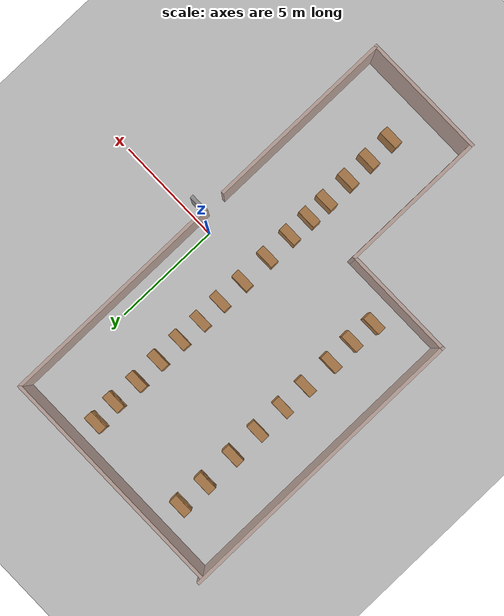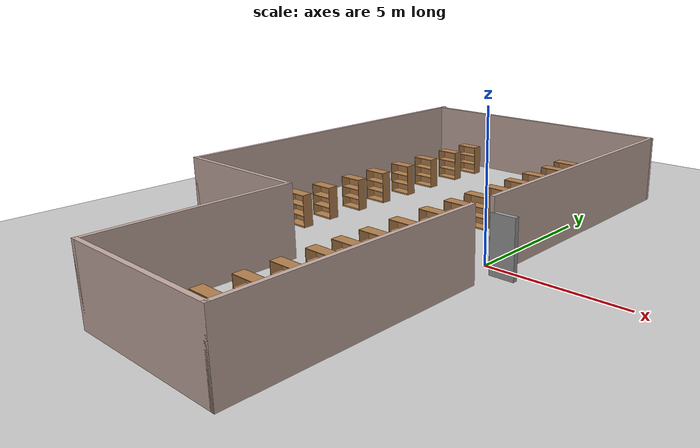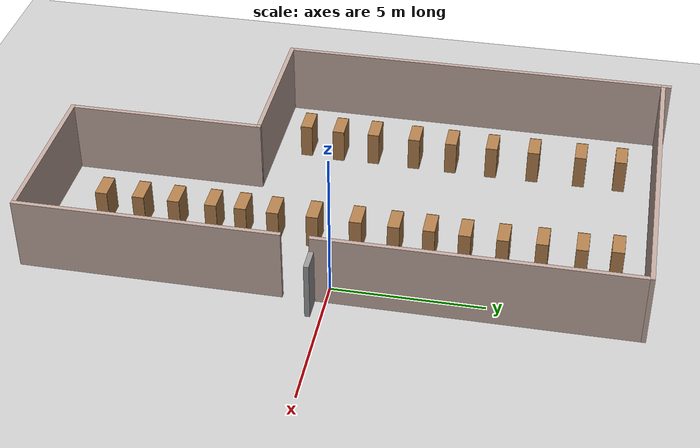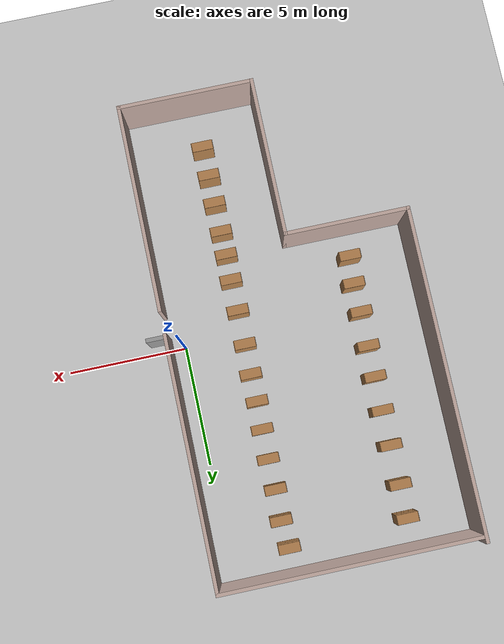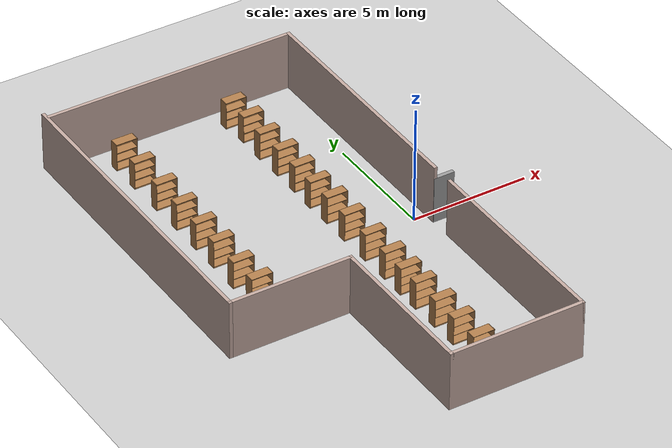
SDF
<sdf version="1.7">
 <world name="default">
  <light name="sun" type="directional">
   <pose>0 0 10 0 -0 0</pose>
   <diffuse>0.8 0.8 0.8 1</diffuse>
   <specular>0.2 0.2 0.2 1</specular>
   <attenuation>
    <range>1000</range>
    <constant>0.9</constant>
    <linear>0.01</linear>
    <quadratic>0.001</quadratic>
   </attenuation>
   <direction>-0.5 0.1 -0.9</direction>
   <spot><inner_angle>0</inner_angle><outer_angle>0</outer_angle><falloff>0</falloff></spot>
  </light>
  <model name="ground_plane">
   <static>1</static>
   <link name="link">
    <collision name="collision">
     <geometry><plane><normal>0 0 1</normal><size>100 100</size></plane></geometry>
     <surface><friction><ode><mu>100</mu><mu2>50</mu2></ode></friction></surface>
    </collision>
    <visual name="visual">
     <cast_shadows>0</cast_shadows>
     <geometry><plane><normal>0 0 1</normal><size>100 100</size></plane></geometry>
     <material>
      <script><uri>file://media/materials/scripts/gazebo.material</uri><name>Gazebo/Grey</name></script>
     </material>
    </visual>
   </link>
  </model>
  <gravity>0 0 -9.8</gravity>
  <magnetic_field>6e-06 2.3e-05 -4.2e-05</magnetic_field>
  <atmosphere type="adiabatic"/>
  <physics type="ode">
   <max_step_size>0.001</max_step_size>
   <real_time_factor>1</real_time_factor>
   <real_time_update_rate>1000</real_time_update_rate>
  </physics>
  <scene><ambient>0.4 0.4 0.4 1</ambient><background>0.7 0.7 0.7 1</background><shadows>1</shadows></scene>
  <spherical_coordinates>
   <surface_model>EARTH_WGS84</surface_model>
   <latitude_deg>0</latitude_deg>
   <longitude_deg>0</longitude_deg>
   <elevation>0</elevation>
   <heading_deg>0</heading_deg>
  </spherical_coordinates>
  <model name="Library">
   <pose>-4.7482 0.020736 0 0 -0 0</pose>
   <link name="Door_0">
    <collision name="Door_0_Collision">
     <geometry><box><size>0.9 0.17 2</size></box></geometry>
     <pose>0 0 1 0 -0 0</pose>
    </collision>
    <visual name="Door_0_Visual">
     <pose>0 0 1 0 -0 0</pose>
     <geometry><box><size>0.9 0.17 2</size></box></geometry>
     <material>
      <script><uri>file://media/materials/scripts/gazebo.material</uri><name>Gazebo/Grey</name></script>
     </material>
    </visual>
    <pose>5.73366 -0.456007 0 0 -0 0</pose>
   </link>
   <link name="Wall_10">
    <collision name="Wall_10_Collision">
     <geometry><box><size>8.75 0.15 2.5</size></box></geometry>
     <pose>0 0 1.25 0 -0 0</pose>
    </collision>
    <visual name="Wall_10_Visual">
     <pose>0 0 1.25 0 -0 0</pose>
     <geometry><box><size>8.75 0.15 2.5</size></box></geometry>
     <material>
      <script><uri>file://media/materials/scripts/gazebo.material</uri><name>Gazebo/Grey</name></script>
      <ambient>0.760784 0.662745 0.627451 1</ambient>
     </material>
     <meta><layer>0</layer></meta>
    </visual>
    <pose>5.35 -5.8 0 0 -0 1.5708</pose>
   </link>
   <link name="Wall_12">
    <collision name="Wall_12_Collision">
     <geometry><box><size>10.5 0.15 2.5</size></box></geometry>
     <pose>0 0 1.25 0 -0 0</pose>
    </collision>
    <visual name="Wall_12_Visual">
     <pose>0 0 1.25 0 -0 0</pose>
     <geometry><box><size>10.5 0.15 2.5</size></box></geometry>
     <material>
      <script><uri>file://media/materials/scripts/gazebo.material</uri><name>Gazebo/Grey</name></script>
      <ambient>0.760784 0.662745 0.627451 1</ambient>
     </material>
     <meta><layer>0</layer></meta>
    </visual>
    <pose>5.3467 4.71899 0 0 -0 1.5708</pose>
   </link>
   <link name="Wall_13">
    <collision name="Wall_13_Collision">
     <geometry><box><size>10.75 0.15 2.5</size></box></geometry>
     <pose>0 0 1.25 0 -0 0</pose>
    </collision>
    <visual name="Wall_13_Visual">
     <pose>0 0 1.25 0 -0 0</pose>
     <geometry><box><size>10.75 0.15 2.5</size></box></geometry>
     <material>
      <script><uri>file://media/materials/scripts/gazebo.material</uri><name>Gazebo/Grey</name></script>
      <ambient>0.760784 0.662745 0.627451 1</ambient>
     </material>
     <meta><layer>0</layer></meta>
    </visual>
    <pose>0.046696 9.89399 0 0 -0 3.14159</pose>
   </link>
   <link name="Wall_6">
    <collision name="Wall_6_Collision">
     <geometry><box><size>13.75 0.15 2.5</size></box></geometry>
     <pose>0 0 1.25 0 -0 0</pose>
    </collision>
    <visual name="Wall_6_Visual">
     <pose>0 0 1.25 0 -0 0</pose>
     <geometry><box><size>13.75 0.15 2.5</size></box></geometry>
     <material>
      <script><uri>file://media/materials/scripts/gazebo.material</uri><name>Gazebo/Grey</name></script>
      <ambient>0.760784 0.662745 0.627451 1</ambient>
     </material>
     <meta><layer>0</layer></meta>
    </visual>
    <pose>-5.35 3.3 0 0 -0 -1.5708</pose>
   </link>
   <link name="Wall_7">
    <collision name="Wall_7_Collision">
     <geometry><box><size>5.25 0.15 2.5</size></box></geometry>
     <pose>0 0 1.25 0 -0 0</pose>
    </collision>
    <visual name="Wall_7_Visual">
     <pose>0 0 1.25 0 -0 0</pose>
     <geometry><box><size>5.25 0.15 2.5</size></box></geometry>
     <material>
      <script><uri>file://media/materials/scripts/gazebo.material</uri><name>Gazebo/Grey</name></script>
      <ambient>0.760784 0.662745 0.627451 1</ambient>
     </material>
     <meta><layer>0</layer></meta>
    </visual>
    <pose>-2.8 -3.5 0 0 -0 0</pose>
   </link>
   <link name="Wall_8">
    <collision name="Wall_8_Collision">
     <geometry><box><size>6.75 0.15 2.5</size></box></geometry>
     <pose>0 0 1.25 0 -0 0</pose>
    </collision>
    <visual name="Wall_8_Visual">
     <pose>0 0 1.25 0 -0 0</pose>
     <geometry><box><size>6.75 0.15 2.5</size></box></geometry>
     <material>
      <script><uri>file://media/materials/scripts/gazebo.material</uri><name>Gazebo/Grey</name></script>
      <ambient>0.760784 0.662745 0.627451 1</ambient>
     </material>
     <meta><layer>0</layer></meta>
    </visual>
    <pose>-0.25 -6.8 0 0 -0 -1.5708</pose>
   </link>
   <link name="Wall_9">
    <collision name="Wall_9_Collision">
     <geometry><box><size>5.75 0.15 2.5</size></box></geometry>
     <pose>0 0 1.25 0 -0 0</pose>
    </collision>
    <visual name="Wall_9_Visual">
     <pose>0 0 1.25 0 -0 0</pose>
     <geometry><box><size>5.75 0.15 2.5</size></box></geometry>
     <material>
      <script><uri>file://media/materials/scripts/gazebo.material</uri><name>Gazebo/Grey</name></script>
      <ambient>0.760784 0.662745 0.627451 1</ambient>
     </material>
     <meta><layer>0</layer></meta>
    </visual>
    <pose>2.55 -10.1 0 0 -0 0</pose>
   </link>
   <static>1</static>
  </model>
  <model name="bookshelf">
   <static>1</static>
   <link name="link">
    <inertial><mass>1</mass></inertial>
    <collision name="back">
     <pose>0 0.005 0.6 0 -0 0</pose>
     <geometry><box><size>0.9 0.01 1.2</size></box></geometry>
    </collision>
    <visual name="visual1">
     <pose>0 0.005 0.6 0 -0 0</pose>
     <geometry><box><size>0.9 0.01 1.2</size></box></geometry>
     <material>
      <script><uri>file://media/materials/scripts/gazebo.material</uri><name>Gazebo/Wood</name></script>
     </material>
    </visual>
    <collision name="left_side">
     <pose>0.45 -0.195 0.6 0 -0 0</pose>
     <geometry><box><size>0.02 0.4 1.2</size></box></geometry>
    </collision>
    <visual name="visual2">
     <pose>0.45 -0.195 0.6 0 -0 0</pose>
     <geometry><box><size>0.02 0.4 1.2</size></box></geometry>
     <material>
      <script><uri>file://media/materials/scripts/gazebo.material</uri><name>Gazebo/Wood</name></script>
     </material>
    </visual>
    <collision name="right_side">
     <pose>-0.45 -0.195 0.6 0 -0 0</pose>
     <geometry><box><size>0.02 0.4 1.2</size></box></geometry>
    </collision>
    <visual name="visual3">
     <pose>-0.45 -0.195 0.6 0 -0 0</pose>
     <geometry><box><size>0.02 0.4 1.2</size></box></geometry>
     <material>
      <script><uri>file://media/materials/scripts/gazebo.material</uri><name>Gazebo/Wood</name></script>
     </material>
    </visual>
    <collision name="bottom">
     <pose>0 -0.195 0.03 0 -0 0</pose>
     <geometry><box><size>0.88 0.4 0.06</size></box></geometry>
    </collision>
    <visual name="visual4">
     <pose>0 -0.195 0.03 0 -0 0</pose>
     <geometry><box><size>0.88 0.4 0.06</size></box></geometry>
     <material>
      <script><uri>file://media/materials/scripts/gazebo.material</uri><name>Gazebo/Wood</name></script>
     </material>
    </visual>
    <collision name="top">
     <pose>0 -0.195 1.19 0 -0 0</pose>
     <geometry><box><size>0.88 0.4 0.02</size></box></geometry>
    </collision>
    <visual name="visual5">
     <pose>0 -0.195 1.19 0 -0 0</pose>
     <geometry><box><size>0.88 0.4 0.02</size></box></geometry>
     <material>
      <script><uri>file://media/materials/scripts/gazebo.material</uri><name>Gazebo/Wood</name></script>
     </material>
    </visual>
    <collision name="low_shelf">
     <pose>0 -0.195 0.43 0 -0 0</pose>
     <geometry><box><size>0.88 0.4 0.02</size></box></geometry>
    </collision>
    <visual name="visual6">
     <pose>0 -0.195 0.43 0 -0 0</pose>
     <geometry><box><size>0.88 0.4 0.02</size></box></geometry>
     <material>
      <script><uri>file://media/materials/scripts/gazebo.material</uri><name>Gazebo/Wood</name></script>
     </material>
    </visual>
    <collision name="high_shelf">
     <pose>0 -0.195 0.8 0 -0 0</pose>
     <geometry><box><size>0.88 0.4 0.02</size></box></geometry>
    </collision>
    <visual name="visual7">
     <pose>0 -0.195 0.8 0 -0 0</pose>
     <geometry><box><size>0.88 0.4 0.02</size></box></geometry>
     <material>
      <script><uri>file://media/materials/scripts/gazebo.material</uri><name>Gazebo/Wood</name></script>
     </material>
    </visual>
   </link>
   <pose>-7.44995 -0.945511 0 0 -0 0</pose>
  </model>
  <model name="bookshelf_0">
   <static>1</static>
   <link name="link">
    <inertial><mass>1</mass></inertial>
    <collision name="back">
     <pose>0 0.005 0.6 0 -0 0</pose>
     <geometry><box><size>0.9 0.01 1.2</size></box></geometry>
    </collision>
    <visual name="visual1">
     <pose>0 0.005 0.6 0 -0 0</pose>
     <geometry><box><size>0.9 0.01 1.2</size></box></geometry>
     <material>
      <script><uri>file://media/materials/scripts/gazebo.material</uri><name>Gazebo/Wood</name></script>
     </material>
    </visual>
    <collision name="left_side">
     <pose>0.45 -0.195 0.6 0 -0 0</pose>
     <geometry><box><size>0.02 0.4 1.2</size></box></geometry>
    </collision>
    <visual name="visual2">
     <pose>0.45 -0.195 0.6 0 -0 0</pose>
     <geometry><box><size>0.02 0.4 1.2</size></box></geometry>
     <material>
      <script><uri>file://media/materials/scripts/gazebo.material</uri><name>Gazebo/Wood</name></script>
     </material>
    </visual>
    <collision name="right_side">
     <pose>-0.45 -0.195 0.6 0 -0 0</pose>
     <geometry><box><size>0.02 0.4 1.2</size></box></geometry>
    </collision>
    <visual name="visual3">
     <pose>-0.45 -0.195 0.6 0 -0 0</pose>
     <geometry><box><size>0.02 0.4 1.2</size></box></geometry>
     <material>
      <script><uri>file://media/materials/scripts/gazebo.material</uri><name>Gazebo/Wood</name></script>
     </material>
    </visual>
    <collision name="bottom">
     <pose>0 -0.195 0.03 0 -0 0</pose>
     <geometry><box><size>0.88 0.4 0.06</size></box></geometry>
    </collision>
    <visual name="visual4">
     <pose>0 -0.195 0.03 0 -0 0</pose>
     <geometry><box><size>0.88 0.4 0.06</size></box></geometry>
     <material>
      <script><uri>file://media/materials/scripts/gazebo.material</uri><name>Gazebo/Wood</name></script>
     </material>
    </visual>
    <collision name="top">
     <pose>0 -0.195 1.19 0 -0 0</pose>
     <geometry><box><size>0.88 0.4 0.02</size></box></geometry>
    </collision>
    <visual name="visual5">
     <pose>0 -0.195 1.19 0 -0 0</pose>
     <geometry><box><size>0.88 0.4 0.02</size></box></geometry>
     <material>
      <script><uri>file://media/materials/scripts/gazebo.material</uri><name>Gazebo/Wood</name></script>
     </material>
    </visual>
    <collision name="low_shelf">
     <pose>0 -0.195 0.43 0 -0 0</pose>
     <geometry><box><size>0.88 0.4 0.02</size></box></geometry>
    </collision>
    <visual name="visual6">
     <pose>0 -0.195 0.43 0 -0 0</pose>
     <geometry><box><size>0.88 0.4 0.02</size></box></geometry>
     <material>
      <script><uri>file://media/materials/scripts/gazebo.material</uri><name>Gazebo/Wood</name></script>
     </material>
    </visual>
    <collision name="high_shelf">
     <pose>0 -0.195 0.8 0 -0 0</pose>
     <geometry><box><size>0.88 0.4 0.02</size></box></geometry>
    </collision>
    <visual name="visual7">
     <pose>0 -0.195 0.8 0 -0 0</pose>
     <geometry><box><size>0.88 0.4 0.02</size></box></geometry>
     <material>
      <script><uri>file://media/materials/scripts/gazebo.material</uri><name>Gazebo/Wood</name></script>
     </material>
    </visual>
   </link>
   <pose>-7.44247 8.93177 0 0 -0 0</pose>
  </model>
  <model name="bookshelf_1">
   <static>1</static>
   <link name="link">
    <inertial><mass>1</mass></inertial>
    <collision name="back">
     <pose>0 0.005 0.6 0 -0 0</pose>
     <geometry><box><size>0.9 0.01 1.2</size></box></geometry>
    </collision>
    <visual name="visual1">
     <pose>0 0.005 0.6 0 -0 0</pose>
     <geometry><box><size>0.9 0.01 1.2</size></box></geometry>
     <material>
      <script><uri>file://media/materials/scripts/gazebo.material</uri><name>Gazebo/Wood</name></script>
     </material>
    </visual>
    <collision name="left_side">
     <pose>0.45 -0.195 0.6 0 -0 0</pose>
     <geometry><box><size>0.02 0.4 1.2</size></box></geometry>
    </collision>
    <visual name="visual2">
     <pose>0.45 -0.195 0.6 0 -0 0</pose>
     <geometry><box><size>0.02 0.4 1.2</size></box></geometry>
     <material>
      <script><uri>file://media/materials/scripts/gazebo.material</uri><name>Gazebo/Wood</name></script>
     </material>
    </visual>
    <collision name="right_side">
     <pose>-0.45 -0.195 0.6 0 -0 0</pose>
     <geometry><box><size>0.02 0.4 1.2</size></box></geometry>
    </collision>
    <visual name="visual3">
     <pose>-0.45 -0.195 0.6 0 -0 0</pose>
     <geometry><box><size>0.02 0.4 1.2</size></box></geometry>
     <material>
      <script><uri>file://media/materials/scripts/gazebo.material</uri><name>Gazebo/Wood</name></script>
     </material>
    </visual>
    <collision name="bottom">
     <pose>0 -0.195 0.03 0 -0 0</pose>
     <geometry><box><size>0.88 0.4 0.06</size></box></geometry>
    </collision>
    <visual name="visual4">
     <pose>0 -0.195 0.03 0 -0 0</pose>
     <geometry><box><size>0.88 0.4 0.06</size></box></geometry>
     <material>
      <script><uri>file://media/materials/scripts/gazebo.material</uri><name>Gazebo/Wood</name></script>
     </material>
    </visual>
    <collision name="top">
     <pose>0 -0.195 1.19 0 -0 0</pose>
     <geometry><box><size>0.88 0.4 0.02</size></box></geometry>
    </collision>
    <visual name="visual5">
     <pose>0 -0.195 1.19 0 -0 0</pose>
     <geometry><box><size>0.88 0.4 0.02</size></box></geometry>
     <material>
      <script><uri>file://media/materials/scripts/gazebo.material</uri><name>Gazebo/Wood</name></script>
     </material>
    </visual>
    <collision name="low_shelf">
     <pose>0 -0.195 0.43 0 -0 0</pose>
     <geometry><box><size>0.88 0.4 0.02</size></box></geometry>
    </collision>
    <visual name="visual6">
     <pose>0 -0.195 0.43 0 -0 0</pose>
     <geometry><box><size>0.88 0.4 0.02</size></box></geometry>
     <material>
      <script><uri>file://media/materials/scripts/gazebo.material</uri><name>Gazebo/Wood</name></script>
     </material>
    </visual>
    <collision name="high_shelf">
     <pose>0 -0.195 0.8 0 -0 0</pose>
     <geometry><box><size>0.88 0.4 0.02</size></box></geometry>
    </collision>
    <visual name="visual7">
     <pose>0 -0.195 0.8 0 -0 0</pose>
     <geometry><box><size>0.88 0.4 0.02</size></box></geometry>
     <material>
      <script><uri>file://media/materials/scripts/gazebo.material</uri><name>Gazebo/Wood</name></script>
     </material>
    </visual>
   </link>
   <pose>-7.45904 7.54943 0 0 -0 0</pose>
  </model>
  <model name="bookshelf_2">
   <static>1</static>
   <link name="link">
    <inertial><mass>1</mass></inertial>
    <collision name="back">
     <pose>0 0.005 0.6 0 -0 0</pose>
     <geometry><box><size>0.9 0.01 1.2</size></box></geometry>
    </collision>
    <visual name="visual1">
     <pose>0 0.005 0.6 0 -0 0</pose>
     <geometry><box><size>0.9 0.01 1.2</size></box></geometry>
     <material>
      <script><uri>file://media/materials/scripts/gazebo.material</uri><name>Gazebo/Wood</name></script>
     </material>
    </visual>
    <collision name="left_side">
     <pose>0.45 -0.195 0.6 0 -0 0</pose>
     <geometry><box><size>0.02 0.4 1.2</size></box></geometry>
    </collision>
    <visual name="visual2">
     <pose>0.45 -0.195 0.6 0 -0 0</pose>
     <geometry><box><size>0.02 0.4 1.2</size></box></geometry>
     <material>
      <script><uri>file://media/materials/scripts/gazebo.material</uri><name>Gazebo/Wood</name></script>
     </material>
    </visual>
    <collision name="right_side">
     <pose>-0.45 -0.195 0.6 0 -0 0</pose>
     <geometry><box><size>0.02 0.4 1.2</size></box></geometry>
    </collision>
    <visual name="visual3">
     <pose>-0.45 -0.195 0.6 0 -0 0</pose>
     <geometry><box><size>0.02 0.4 1.2</size></box></geometry>
     <material>
      <script><uri>file://media/materials/scripts/gazebo.material</uri><name>Gazebo/Wood</name></script>
     </material>
    </visual>
    <collision name="bottom">
     <pose>0 -0.195 0.03 0 -0 0</pose>
     <geometry><box><size>0.88 0.4 0.06</size></box></geometry>
    </collision>
    <visual name="visual4">
     <pose>0 -0.195 0.03 0 -0 0</pose>
     <geometry><box><size>0.88 0.4 0.06</size></box></geometry>
     <material>
      <script><uri>file://media/materials/scripts/gazebo.material</uri><name>Gazebo/Wood</name></script>
     </material>
    </visual>
    <collision name="top">
     <pose>0 -0.195 1.19 0 -0 0</pose>
     <geometry><box><size>0.88 0.4 0.02</size></box></geometry>
    </collision>
    <visual name="visual5">
     <pose>0 -0.195 1.19 0 -0 0</pose>
     <geometry><box><size>0.88 0.4 0.02</size></box></geometry>
     <material>
      <script><uri>file://media/materials/scripts/gazebo.material</uri><name>Gazebo/Wood</name></script>
     </material>
    </visual>
    <collision name="low_shelf">
     <pose>0 -0.195 0.43 0 -0 0</pose>
     <geometry><box><size>0.88 0.4 0.02</size></box></geometry>
    </collision>
    <visual name="visual6">
     <pose>0 -0.195 0.43 0 -0 0</pose>
     <geometry><box><size>0.88 0.4 0.02</size></box></geometry>
     <material>
      <script><uri>file://media/materials/scripts/gazebo.material</uri><name>Gazebo/Wood</name></script>
     </material>
    </visual>
    <collision name="high_shelf">
     <pose>0 -0.195 0.8 0 -0 0</pose>
     <geometry><box><size>0.88 0.4 0.02</size></box></geometry>
    </collision>
    <visual name="visual7">
     <pose>0 -0.195 0.8 0 -0 0</pose>
     <geometry><box><size>0.88 0.4 0.02</size></box></geometry>
     <material>
      <script><uri>file://media/materials/scripts/gazebo.material</uri><name>Gazebo/Wood</name></script>
     </material>
    </visual>
   </link>
   <pose>-7.44287 5.92854 0 0 -0 0</pose>
  </model>
  <model name="bookshelf_3">
   <static>1</static>
   <link name="link">
    <inertial><mass>1</mass></inertial>
    <collision name="back">
     <pose>0 0.005 0.6 0 -0 0</pose>
     <geometry><box><size>0.9 0.01 1.2</size></box></geometry>
    </collision>
    <visual name="visual1">
     <pose>0 0.005 0.6 0 -0 0</pose>
     <geometry><box><size>0.9 0.01 1.2</size></box></geometry>
     <material>
      <script><uri>file://media/materials/scripts/gazebo.material</uri><name>Gazebo/Wood</name></script>
     </material>
    </visual>
    <collision name="left_side">
     <pose>0.45 -0.195 0.6 0 -0 0</pose>
     <geometry><box><size>0.02 0.4 1.2</size></box></geometry>
    </collision>
    <visual name="visual2">
     <pose>0.45 -0.195 0.6 0 -0 0</pose>
     <geometry><box><size>0.02 0.4 1.2</size></box></geometry>
     <material>
      <script><uri>file://media/materials/scripts/gazebo.material</uri><name>Gazebo/Wood</name></script>
     </material>
    </visual>
    <collision name="right_side">
     <pose>-0.45 -0.195 0.6 0 -0 0</pose>
     <geometry><box><size>0.02 0.4 1.2</size></box></geometry>
    </collision>
    <visual name="visual3">
     <pose>-0.45 -0.195 0.6 0 -0 0</pose>
     <geometry><box><size>0.02 0.4 1.2</size></box></geometry>
     <material>
      <script><uri>file://media/materials/scripts/gazebo.material</uri><name>Gazebo/Wood</name></script>
     </material>
    </visual>
    <collision name="bottom">
     <pose>0 -0.195 0.03 0 -0 0</pose>
     <geometry><box><size>0.88 0.4 0.06</size></box></geometry>
    </collision>
    <visual name="visual4">
     <pose>0 -0.195 0.03 0 -0 0</pose>
     <geometry><box><size>0.88 0.4 0.06</size></box></geometry>
     <material>
      <script><uri>file://media/materials/scripts/gazebo.material</uri><name>Gazebo/Wood</name></script>
     </material>
    </visual>
    <collision name="top">
     <pose>0 -0.195 1.19 0 -0 0</pose>
     <geometry><box><size>0.88 0.4 0.02</size></box></geometry>
    </collision>
    <visual name="visual5">
     <pose>0 -0.195 1.19 0 -0 0</pose>
     <geometry><box><size>0.88 0.4 0.02</size></box></geometry>
     <material>
      <script><uri>file://media/materials/scripts/gazebo.material</uri><name>Gazebo/Wood</name></script>
     </material>
    </visual>
    <collision name="low_shelf">
     <pose>0 -0.195 0.43 0 -0 0</pose>
     <geometry><box><size>0.88 0.4 0.02</size></box></geometry>
    </collision>
    <visual name="visual6">
     <pose>0 -0.195 0.43 0 -0 0</pose>
     <geometry><box><size>0.88 0.4 0.02</size></box></geometry>
     <material>
      <script><uri>file://media/materials/scripts/gazebo.material</uri><name>Gazebo/Wood</name></script>
     </material>
    </visual>
    <collision name="high_shelf">
     <pose>0 -0.195 0.8 0 -0 0</pose>
     <geometry><box><size>0.88 0.4 0.02</size></box></geometry>
    </collision>
    <visual name="visual7">
     <pose>0 -0.195 0.8 0 -0 0</pose>
     <geometry><box><size>0.88 0.4 0.02</size></box></geometry>
     <material>
      <script><uri>file://media/materials/scripts/gazebo.material</uri><name>Gazebo/Wood</name></script>
     </material>
    </visual>
   </link>
   <pose>-7.43021 4.47652 0 0 -0 0</pose>
  </model>
  <model name="bookshelf_4">
   <static>1</static>
   <link name="link">
    <inertial><mass>1</mass></inertial>
    <collision name="back">
     <pose>0 0.005 0.6 0 -0 0</pose>
     <geometry><box><size>0.9 0.01 1.2</size></box></geometry>
    </collision>
    <visual name="visual1">
     <pose>0 0.005 0.6 0 -0 0</pose>
     <geometry><box><size>0.9 0.01 1.2</size></box></geometry>
     <material>
      <script><uri>file://media/materials/scripts/gazebo.material</uri><name>Gazebo/Wood</name></script>
     </material>
    </visual>
    <collision name="left_side">
     <pose>0.45 -0.195 0.6 0 -0 0</pose>
     <geometry><box><size>0.02 0.4 1.2</size></box></geometry>
    </collision>
    <visual name="visual2">
     <pose>0.45 -0.195 0.6 0 -0 0</pose>
     <geometry><box><size>0.02 0.4 1.2</size></box></geometry>
     <material>
      <script><uri>file://media/materials/scripts/gazebo.material</uri><name>Gazebo/Wood</name></script>
     </material>
    </visual>
    <collision name="right_side">
     <pose>-0.45 -0.195 0.6 0 -0 0</pose>
     <geometry><box><size>0.02 0.4 1.2</size></box></geometry>
    </collision>
    <visual name="visual3">
     <pose>-0.45 -0.195 0.6 0 -0 0</pose>
     <geometry><box><size>0.02 0.4 1.2</size></box></geometry>
     <material>
      <script><uri>file://media/materials/scripts/gazebo.material</uri><name>Gazebo/Wood</name></script>
     </material>
    </visual>
    <collision name="bottom">
     <pose>0 -0.195 0.03 0 -0 0</pose>
     <geometry><box><size>0.88 0.4 0.06</size></box></geometry>
    </collision>
    <visual name="visual4">
     <pose>0 -0.195 0.03 0 -0 0</pose>
     <geometry><box><size>0.88 0.4 0.06</size></box></geometry>
     <material>
      <script><uri>file://media/materials/scripts/gazebo.material</uri><name>Gazebo/Wood</name></script>
     </material>
    </visual>
    <collision name="top">
     <pose>0 -0.195 1.19 0 -0 0</pose>
     <geometry><box><size>0.88 0.4 0.02</size></box></geometry>
    </collision>
    <visual name="visual5">
     <pose>0 -0.195 1.19 0 -0 0</pose>
     <geometry><box><size>0.88 0.4 0.02</size></box></geometry>
     <material>
      <script><uri>file://media/materials/scripts/gazebo.material</uri><name>Gazebo/Wood</name></script>
     </material>
    </visual>
    <collision name="low_shelf">
     <pose>0 -0.195 0.43 0 -0 0</pose>
     <geometry><box><size>0.88 0.4 0.02</size></box></geometry>
    </collision>
    <visual name="visual6">
     <pose>0 -0.195 0.43 0 -0 0</pose>
     <geometry><box><size>0.88 0.4 0.02</size></box></geometry>
     <material>
      <script><uri>file://media/materials/scripts/gazebo.material</uri><name>Gazebo/Wood</name></script>
     </material>
    </visual>
    <collision name="high_shelf">
     <pose>0 -0.195 0.8 0 -0 0</pose>
     <geometry><box><size>0.88 0.4 0.02</size></box></geometry>
    </collision>
    <visual name="visual7">
     <pose>0 -0.195 0.8 0 -0 0</pose>
     <geometry><box><size>0.88 0.4 0.02</size></box></geometry>
     <material>
      <script><uri>file://media/materials/scripts/gazebo.material</uri><name>Gazebo/Wood</name></script>
     </material>
    </visual>
   </link>
   <pose>-7.44126 3.05021 0 0 -0 0</pose>
  </model>
  <model name="bookshelf_5">
   <static>1</static>
   <link name="link">
    <inertial><mass>1</mass></inertial>
    <collision name="back">
     <pose>0 0.005 0.6 0 -0 0</pose>
     <geometry><box><size>0.9 0.01 1.2</size></box></geometry>
    </collision>
    <visual name="visual1">
     <pose>0 0.005 0.6 0 -0 0</pose>
     <geometry><box><size>0.9 0.01 1.2</size></box></geometry>
     <material>
      <script><uri>file://media/materials/scripts/gazebo.material</uri><name>Gazebo/Wood</name></script>
     </material>
    </visual>
    <collision name="left_side">
     <pose>0.45 -0.195 0.6 0 -0 0</pose>
     <geometry><box><size>0.02 0.4 1.2</size></box></geometry>
    </collision>
    <visual name="visual2">
     <pose>0.45 -0.195 0.6 0 -0 0</pose>
     <geometry><box><size>0.02 0.4 1.2</size></box></geometry>
     <material>
      <script><uri>file://media/materials/scripts/gazebo.material</uri><name>Gazebo/Wood</name></script>
     </material>
    </visual>
    <collision name="right_side">
     <pose>-0.45 -0.195 0.6 0 -0 0</pose>
     <geometry><box><size>0.02 0.4 1.2</size></box></geometry>
    </collision>
    <visual name="visual3">
     <pose>-0.45 -0.195 0.6 0 -0 0</pose>
     <geometry><box><size>0.02 0.4 1.2</size></box></geometry>
     <material>
      <script><uri>file://media/materials/scripts/gazebo.material</uri><name>Gazebo/Wood</name></script>
     </material>
    </visual>
    <collision name="bottom">
     <pose>0 -0.195 0.03 0 -0 0</pose>
     <geometry><box><size>0.88 0.4 0.06</size></box></geometry>
    </collision>
    <visual name="visual4">
     <pose>0 -0.195 0.03 0 -0 0</pose>
     <geometry><box><size>0.88 0.4 0.06</size></box></geometry>
     <material>
      <script><uri>file://media/materials/scripts/gazebo.material</uri><name>Gazebo/Wood</name></script>
     </material>
    </visual>
    <collision name="top">
     <pose>0 -0.195 1.19 0 -0 0</pose>
     <geometry><box><size>0.88 0.4 0.02</size></box></geometry>
    </collision>
    <visual name="visual5">
     <pose>0 -0.195 1.19 0 -0 0</pose>
     <geometry><box><size>0.88 0.4 0.02</size></box></geometry>
     <material>
      <script><uri>file://media/materials/scripts/gazebo.material</uri><name>Gazebo/Wood</name></script>
     </material>
    </visual>
    <collision name="low_shelf">
     <pose>0 -0.195 0.43 0 -0 0</pose>
     <geometry><box><size>0.88 0.4 0.02</size></box></geometry>
    </collision>
    <visual name="visual6">
     <pose>0 -0.195 0.43 0 -0 0</pose>
     <geometry><box><size>0.88 0.4 0.02</size></box></geometry>
     <material>
      <script><uri>file://media/materials/scripts/gazebo.material</uri><name>Gazebo/Wood</name></script>
     </material>
    </visual>
    <collision name="high_shelf">
     <pose>0 -0.195 0.8 0 -0 0</pose>
     <geometry><box><size>0.88 0.4 0.02</size></box></geometry>
    </collision>
    <visual name="visual7">
     <pose>0 -0.195 0.8 0 -0 0</pose>
     <geometry><box><size>0.88 0.4 0.02</size></box></geometry>
     <material>
      <script><uri>file://media/materials/scripts/gazebo.material</uri><name>Gazebo/Wood</name></script>
     </material>
    </visual>
   </link>
   <pose>-7.4542 1.74877 0 0 -0 0</pose>
  </model>
  <model name="bookshelf_6">
   <static>1</static>
   <link name="link">
    <inertial><mass>1</mass></inertial>
    <collision name="back">
     <pose>0 0.005 0.6 0 -0 0</pose>
     <geometry><box><size>0.9 0.01 1.2</size></box></geometry>
    </collision>
    <visual name="visual1">
     <pose>0 0.005 0.6 0 -0 0</pose>
     <geometry><box><size>0.9 0.01 1.2</size></box></geometry>
     <material>
      <script><uri>file://media/materials/scripts/gazebo.material</uri><name>Gazebo/Wood</name></script>
     </material>
    </visual>
    <collision name="left_side">
     <pose>0.45 -0.195 0.6 0 -0 0</pose>
     <geometry><box><size>0.02 0.4 1.2</size></box></geometry>
    </collision>
    <visual name="visual2">
     <pose>0.45 -0.195 0.6 0 -0 0</pose>
     <geometry><box><size>0.02 0.4 1.2</size></box></geometry>
     <material>
      <script><uri>file://media/materials/scripts/gazebo.material</uri><name>Gazebo/Wood</name></script>
     </material>
    </visual>
    <collision name="right_side">
     <pose>-0.45 -0.195 0.6 0 -0 0</pose>
     <geometry><box><size>0.02 0.4 1.2</size></box></geometry>
    </collision>
    <visual name="visual3">
     <pose>-0.45 -0.195 0.6 0 -0 0</pose>
     <geometry><box><size>0.02 0.4 1.2</size></box></geometry>
     <material>
      <script><uri>file://media/materials/scripts/gazebo.material</uri><name>Gazebo/Wood</name></script>
     </material>
    </visual>
    <collision name="bottom">
     <pose>0 -0.195 0.03 0 -0 0</pose>
     <geometry><box><size>0.88 0.4 0.06</size></box></geometry>
    </collision>
    <visual name="visual4">
     <pose>0 -0.195 0.03 0 -0 0</pose>
     <geometry><box><size>0.88 0.4 0.06</size></box></geometry>
     <material>
      <script><uri>file://media/materials/scripts/gazebo.material</uri><name>Gazebo/Wood</name></script>
     </material>
    </visual>
    <collision name="top">
     <pose>0 -0.195 1.19 0 -0 0</pose>
     <geometry><box><size>0.88 0.4 0.02</size></box></geometry>
    </collision>
    <visual name="visual5">
     <pose>0 -0.195 1.19 0 -0 0</pose>
     <geometry><box><size>0.88 0.4 0.02</size></box></geometry>
     <material>
      <script><uri>file://media/materials/scripts/gazebo.material</uri><name>Gazebo/Wood</name></script>
     </material>
    </visual>
    <collision name="low_shelf">
     <pose>0 -0.195 0.43 0 -0 0</pose>
     <geometry><box><size>0.88 0.4 0.02</size></box></geometry>
    </collision>
    <visual name="visual6">
     <pose>0 -0.195 0.43 0 -0 0</pose>
     <geometry><box><size>0.88 0.4 0.02</size></box></geometry>
     <material>
      <script><uri>file://media/materials/scripts/gazebo.material</uri><name>Gazebo/Wood</name></script>
     </material>
    </visual>
    <collision name="high_shelf">
     <pose>0 -0.195 0.8 0 -0 0</pose>
     <geometry><box><size>0.88 0.4 0.02</size></box></geometry>
    </collision>
    <visual name="visual7">
     <pose>0 -0.195 0.8 0 -0 0</pose>
     <geometry><box><size>0.88 0.4 0.02</size></box></geometry>
     <material>
      <script><uri>file://media/materials/scripts/gazebo.material</uri><name>Gazebo/Wood</name></script>
     </material>
    </visual>
   </link>
   <pose>-7.48414 0.295837 0 0 -0 0</pose>
  </model>
  <model name="bookshelf_7">
   <static>1</static>
   <link name="link">
    <inertial><mass>1</mass></inertial>
    <collision name="back">
     <pose>0 0.005 0.6 0 -0 0</pose>
     <geometry><box><size>0.9 0.01 1.2</size></box></geometry>
    </collision>
    <visual name="visual1">
     <pose>0 0.005 0.6 0 -0 0</pose>
     <geometry><box><size>0.9 0.01 1.2</size></box></geometry>
     <material>
      <script><uri>file://media/materials/scripts/gazebo.material</uri><name>Gazebo/Wood</name></script>
     </material>
    </visual>
    <collision name="left_side">
     <pose>0.45 -0.195 0.6 0 -0 0</pose>
     <geometry><box><size>0.02 0.4 1.2</size></box></geometry>
    </collision>
    <visual name="visual2">
     <pose>0.45 -0.195 0.6 0 -0 0</pose>
     <geometry><box><size>0.02 0.4 1.2</size></box></geometry>
     <material>
      <script><uri>file://media/materials/scripts/gazebo.material</uri><name>Gazebo/Wood</name></script>
     </material>
    </visual>
    <collision name="right_side">
     <pose>-0.45 -0.195 0.6 0 -0 0</pose>
     <geometry><box><size>0.02 0.4 1.2</size></box></geometry>
    </collision>
    <visual name="visual3">
     <pose>-0.45 -0.195 0.6 0 -0 0</pose>
     <geometry><box><size>0.02 0.4 1.2</size></box></geometry>
     <material>
      <script><uri>file://media/materials/scripts/gazebo.material</uri><name>Gazebo/Wood</name></script>
     </material>
    </visual>
    <collision name="bottom">
     <pose>0 -0.195 0.03 0 -0 0</pose>
     <geometry><box><size>0.88 0.4 0.06</size></box></geometry>
    </collision>
    <visual name="visual4">
     <pose>0 -0.195 0.03 0 -0 0</pose>
     <geometry><box><size>0.88 0.4 0.06</size></box></geometry>
     <material>
      <script><uri>file://media/materials/scripts/gazebo.material</uri><name>Gazebo/Wood</name></script>
     </material>
    </visual>
    <collision name="top">
     <pose>0 -0.195 1.19 0 -0 0</pose>
     <geometry><box><size>0.88 0.4 0.02</size></box></geometry>
    </collision>
    <visual name="visual5">
     <pose>0 -0.195 1.19 0 -0 0</pose>
     <geometry><box><size>0.88 0.4 0.02</size></box></geometry>
     <material>
      <script><uri>file://media/materials/scripts/gazebo.material</uri><name>Gazebo/Wood</name></script>
     </material>
    </visual>
    <collision name="low_shelf">
     <pose>0 -0.195 0.43 0 -0 0</pose>
     <geometry><box><size>0.88 0.4 0.02</size></box></geometry>
    </collision>
    <visual name="visual6">
     <pose>0 -0.195 0.43 0 -0 0</pose>
     <geometry><box><size>0.88 0.4 0.02</size></box></geometry>
     <material>
      <script><uri>file://media/materials/scripts/gazebo.material</uri><name>Gazebo/Wood</name></script>
     </material>
    </visual>
    <collision name="high_shelf">
     <pose>0 -0.195 0.8 0 -0 0</pose>
     <geometry><box><size>0.88 0.4 0.02</size></box></geometry>
    </collision>
    <visual name="visual7">
     <pose>0 -0.195 0.8 0 -0 0</pose>
     <geometry><box><size>0.88 0.4 0.02</size></box></geometry>
     <material>
      <script><uri>file://media/materials/scripts/gazebo.material</uri><name>Gazebo/Wood</name></script>
     </material>
    </visual>
   </link>
   <pose>-7.54555 -2.11867 0 0 -0 0</pose>
  </model>
  <model name="bookshelf_8">
   <static>1</static>
   <link name="link">
    <inertial><mass>1</mass></inertial>
    <collision name="back">
     <pose>0 0.005 0.6 0 -0 0</pose>
     <geometry><box><size>0.9 0.01 1.2</size></box></geometry>
    </collision>
    <visual name="visual1">
     <pose>0 0.005 0.6 0 -0 0</pose>
     <geometry><box><size>0.9 0.01 1.2</size></box></geometry>
     <material>
      <script><uri>file://media/materials/scripts/gazebo.material</uri><name>Gazebo/Wood</name></script>
     </material>
    </visual>
    <collision name="left_side">
     <pose>0.45 -0.195 0.6 0 -0 0</pose>
     <geometry><box><size>0.02 0.4 1.2</size></box></geometry>
    </collision>
    <visual name="visual2">
     <pose>0.45 -0.195 0.6 0 -0 0</pose>
     <geometry><box><size>0.02 0.4 1.2</size></box></geometry>
     <material>
      <script><uri>file://media/materials/scripts/gazebo.material</uri><name>Gazebo/Wood</name></script>
     </material>
    </visual>
    <collision name="right_side">
     <pose>-0.45 -0.195 0.6 0 -0 0</pose>
     <geometry><box><size>0.02 0.4 1.2</size></box></geometry>
    </collision>
    <visual name="visual3">
     <pose>-0.45 -0.195 0.6 0 -0 0</pose>
     <geometry><box><size>0.02 0.4 1.2</size></box></geometry>
     <material>
      <script><uri>file://media/materials/scripts/gazebo.material</uri><name>Gazebo/Wood</name></script>
     </material>
    </visual>
    <collision name="bottom">
     <pose>0 -0.195 0.03 0 -0 0</pose>
     <geometry><box><size>0.88 0.4 0.06</size></box></geometry>
    </collision>
    <visual name="visual4">
     <pose>0 -0.195 0.03 0 -0 0</pose>
     <geometry><box><size>0.88 0.4 0.06</size></box></geometry>
     <material>
      <script><uri>file://media/materials/scripts/gazebo.material</uri><name>Gazebo/Wood</name></script>
     </material>
    </visual>
    <collision name="top">
     <pose>0 -0.195 1.19 0 -0 0</pose>
     <geometry><box><size>0.88 0.4 0.02</size></box></geometry>
    </collision>
    <visual name="visual5">
     <pose>0 -0.195 1.19 0 -0 0</pose>
     <geometry><box><size>0.88 0.4 0.02</size></box></geometry>
     <material>
      <script><uri>file://media/materials/scripts/gazebo.material</uri><name>Gazebo/Wood</name></script>
     </material>
    </visual>
    <collision name="low_shelf">
     <pose>0 -0.195 0.43 0 -0 0</pose>
     <geometry><box><size>0.88 0.4 0.02</size></box></geometry>
    </collision>
    <visual name="visual6">
     <pose>0 -0.195 0.43 0 -0 0</pose>
     <geometry><box><size>0.88 0.4 0.02</size></box></geometry>
     <material>
      <script><uri>file://media/materials/scripts/gazebo.material</uri><name>Gazebo/Wood</name></script>
     </material>
    </visual>
    <collision name="high_shelf">
     <pose>0 -0.195 0.8 0 -0 0</pose>
     <geometry><box><size>0.88 0.4 0.02</size></box></geometry>
    </collision>
    <visual name="visual7">
     <pose>0 -0.195 0.8 0 -0 0</pose>
     <geometry><box><size>0.88 0.4 0.02</size></box></geometry>
     <material>
      <script><uri>file://media/materials/scripts/gazebo.material</uri><name>Gazebo/Wood</name></script>
     </material>
    </visual>
   </link>
   <pose>-2.44841 -8.00535 0 0 -0 0</pose>
  </model>
  <model name="bookshelf_9">
   <static>1</static>
   <link name="link">
    <inertial><mass>1</mass></inertial>
    <collision name="back">
     <pose>0 0.005 0.6 0 -0 0</pose>
     <geometry><box><size>0.9 0.01 1.2</size></box></geometry>
    </collision>
    <visual name="visual1">
     <pose>0 0.005 0.6 0 -0 0</pose>
     <geometry><box><size>0.9 0.01 1.2</size></box></geometry>
     <material>
      <script><uri>file://media/materials/scripts/gazebo.material</uri><name>Gazebo/Wood</name></script>
     </material>
    </visual>
    <collision name="left_side">
     <pose>0.45 -0.195 0.6 0 -0 0</pose>
     <geometry><box><size>0.02 0.4 1.2</size></box></geometry>
    </collision>
    <visual name="visual2">
     <pose>0.45 -0.195 0.6 0 -0 0</pose>
     <geometry><box><size>0.02 0.4 1.2</size></box></geometry>
     <material>
      <script><uri>file://media/materials/scripts/gazebo.material</uri><name>Gazebo/Wood</name></script>
     </material>
    </visual>
    <collision name="right_side">
     <pose>-0.45 -0.195 0.6 0 -0 0</pose>
     <geometry><box><size>0.02 0.4 1.2</size></box></geometry>
    </collision>
    <visual name="visual3">
     <pose>-0.45 -0.195 0.6 0 -0 0</pose>
     <geometry><box><size>0.02 0.4 1.2</size></box></geometry>
     <material>
      <script><uri>file://media/materials/scripts/gazebo.material</uri><name>Gazebo/Wood</name></script>
     </material>
    </visual>
    <collision name="bottom">
     <pose>0 -0.195 0.03 0 -0 0</pose>
     <geometry><box><size>0.88 0.4 0.06</size></box></geometry>
    </collision>
    <visual name="visual4">
     <pose>0 -0.195 0.03 0 -0 0</pose>
     <geometry><box><size>0.88 0.4 0.06</size></box></geometry>
     <material>
      <script><uri>file://media/materials/scripts/gazebo.material</uri><name>Gazebo/Wood</name></script>
     </material>
    </visual>
    <collision name="top">
     <pose>0 -0.195 1.19 0 -0 0</pose>
     <geometry><box><size>0.88 0.4 0.02</size></box></geometry>
    </collision>
    <visual name="visual5">
     <pose>0 -0.195 1.19 0 -0 0</pose>
     <geometry><box><size>0.88 0.4 0.02</size></box></geometry>
     <material>
      <script><uri>file://media/materials/scripts/gazebo.material</uri><name>Gazebo/Wood</name></script>
     </material>
    </visual>
    <collision name="low_shelf">
     <pose>0 -0.195 0.43 0 -0 0</pose>
     <geometry><box><size>0.88 0.4 0.02</size></box></geometry>
    </collision>
    <visual name="visual6">
     <pose>0 -0.195 0.43 0 -0 0</pose>
     <geometry><box><size>0.88 0.4 0.02</size></box></geometry>
     <material>
      <script><uri>file://media/materials/scripts/gazebo.material</uri><name>Gazebo/Wood</name></script>
     </material>
    </visual>
    <collision name="high_shelf">
     <pose>0 -0.195 0.8 0 -0 0</pose>
     <geometry><box><size>0.88 0.4 0.02</size></box></geometry>
    </collision>
    <visual name="visual7">
     <pose>0 -0.195 0.8 0 -0 0</pose>
     <geometry><box><size>0.88 0.4 0.02</size></box></geometry>
     <material>
      <script><uri>file://media/materials/scripts/gazebo.material</uri><name>Gazebo/Wood</name></script>
     </material>
    </visual>
   </link>
   <pose>-2.45759 -6.7332 0 0 -0 0</pose>
  </model>
  <model name="bookshelf_10">
   <static>1</static>
   <link name="link">
    <inertial><mass>1</mass></inertial>
    <collision name="back">
     <pose>0 0.005 0.6 0 -0 0</pose>
     <geometry><box><size>0.9 0.01 1.2</size></box></geometry>
    </collision>
    <visual name="visual1">
     <pose>0 0.005 0.6 0 -0 0</pose>
     <geometry><box><size>0.9 0.01 1.2</size></box></geometry>
     <material>
      <script><uri>file://media/materials/scripts/gazebo.material</uri><name>Gazebo/Wood</name></script>
     </material>
    </visual>
    <collision name="left_side">
     <pose>0.45 -0.195 0.6 0 -0 0</pose>
     <geometry><box><size>0.02 0.4 1.2</size></box></geometry>
    </collision>
    <visual name="visual2">
     <pose>0.45 -0.195 0.6 0 -0 0</pose>
     <geometry><box><size>0.02 0.4 1.2</size></box></geometry>
     <material>
      <script><uri>file://media/materials/scripts/gazebo.material</uri><name>Gazebo/Wood</name></script>
     </material>
    </visual>
    <collision name="right_side">
     <pose>-0.45 -0.195 0.6 0 -0 0</pose>
     <geometry><box><size>0.02 0.4 1.2</size></box></geometry>
    </collision>
    <visual name="visual3">
     <pose>-0.45 -0.195 0.6 0 -0 0</pose>
     <geometry><box><size>0.02 0.4 1.2</size></box></geometry>
     <material>
      <script><uri>file://media/materials/scripts/gazebo.material</uri><name>Gazebo/Wood</name></script>
     </material>
    </visual>
    <collision name="bottom">
     <pose>0 -0.195 0.03 0 -0 0</pose>
     <geometry><box><size>0.88 0.4 0.06</size></box></geometry>
    </collision>
    <visual name="visual4">
     <pose>0 -0.195 0.03 0 -0 0</pose>
     <geometry><box><size>0.88 0.4 0.06</size></box></geometry>
     <material>
      <script><uri>file://media/materials/scripts/gazebo.material</uri><name>Gazebo/Wood</name></script>
     </material>
    </visual>
    <collision name="top">
     <pose>0 -0.195 1.19 0 -0 0</pose>
     <geometry><box><size>0.88 0.4 0.02</size></box></geometry>
    </collision>
    <visual name="visual5">
     <pose>0 -0.195 1.19 0 -0 0</pose>
     <geometry><box><size>0.88 0.4 0.02</size></box></geometry>
     <material>
      <script><uri>file://media/materials/scripts/gazebo.material</uri><name>Gazebo/Wood</name></script>
     </material>
    </visual>
    <collision name="low_shelf">
     <pose>0 -0.195 0.43 0 -0 0</pose>
     <geometry><box><size>0.88 0.4 0.02</size></box></geometry>
    </collision>
    <visual name="visual6">
     <pose>0 -0.195 0.43 0 -0 0</pose>
     <geometry><box><size>0.88 0.4 0.02</size></box></geometry>
     <material>
      <script><uri>file://media/materials/scripts/gazebo.material</uri><name>Gazebo/Wood</name></script>
     </material>
    </visual>
    <collision name="high_shelf">
     <pose>0 -0.195 0.8 0 -0 0</pose>
     <geometry><box><size>0.88 0.4 0.02</size></box></geometry>
    </collision>
    <visual name="visual7">
     <pose>0 -0.195 0.8 0 -0 0</pose>
     <geometry><box><size>0.88 0.4 0.02</size></box></geometry>
     <material>
      <script><uri>file://media/materials/scripts/gazebo.material</uri><name>Gazebo/Wood</name></script>
     </material>
    </visual>
   </link>
   <pose>-2.45723 -5.51872 0 0 -0 0</pose>
  </model>
  <model name="bookshelf_11">
   <static>1</static>
   <link name="link">
    <inertial><mass>1</mass></inertial>
    <collision name="back">
     <pose>0 0.005 0.6 0 -0 0</pose>
     <geometry><box><size>0.9 0.01 1.2</size></box></geometry>
    </collision>
    <visual name="visual1">
     <pose>0 0.005 0.6 0 -0 0</pose>
     <geometry><box><size>0.9 0.01 1.2</size></box></geometry>
     <material>
      <script><uri>file://media/materials/scripts/gazebo.material</uri><name>Gazebo/Wood</name></script>
     </material>
    </visual>
    <collision name="left_side">
     <pose>0.45 -0.195 0.6 0 -0 0</pose>
     <geometry><box><size>0.02 0.4 1.2</size></box></geometry>
    </collision>
    <visual name="visual2">
     <pose>0.45 -0.195 0.6 0 -0 0</pose>
     <geometry><box><size>0.02 0.4 1.2</size></box></geometry>
     <material>
      <script><uri>file://media/materials/scripts/gazebo.material</uri><name>Gazebo/Wood</name></script>
     </material>
    </visual>
    <collision name="right_side">
     <pose>-0.45 -0.195 0.6 0 -0 0</pose>
     <geometry><box><size>0.02 0.4 1.2</size></box></geometry>
    </collision>
    <visual name="visual3">
     <pose>-0.45 -0.195 0.6 0 -0 0</pose>
     <geometry><box><size>0.02 0.4 1.2</size></box></geometry>
     <material>
      <script><uri>file://media/materials/scripts/gazebo.material</uri><name>Gazebo/Wood</name></script>
     </material>
    </visual>
    <collision name="bottom">
     <pose>0 -0.195 0.03 0 -0 0</pose>
     <geometry><box><size>0.88 0.4 0.06</size></box></geometry>
    </collision>
    <visual name="visual4">
     <pose>0 -0.195 0.03 0 -0 0</pose>
     <geometry><box><size>0.88 0.4 0.06</size></box></geometry>
     <material>
      <script><uri>file://media/materials/scripts/gazebo.material</uri><name>Gazebo/Wood</name></script>
     </material>
    </visual>
    <collision name="top">
     <pose>0 -0.195 1.19 0 -0 0</pose>
     <geometry><box><size>0.88 0.4 0.02</size></box></geometry>
    </collision>
    <visual name="visual5">
     <pose>0 -0.195 1.19 0 -0 0</pose>
     <geometry><box><size>0.88 0.4 0.02</size></box></geometry>
     <material>
      <script><uri>file://media/materials/scripts/gazebo.material</uri><name>Gazebo/Wood</name></script>
     </material>
    </visual>
    <collision name="low_shelf">
     <pose>0 -0.195 0.43 0 -0 0</pose>
     <geometry><box><size>0.88 0.4 0.02</size></box></geometry>
    </collision>
    <visual name="visual6">
     <pose>0 -0.195 0.43 0 -0 0</pose>
     <geometry><box><size>0.88 0.4 0.02</size></box></geometry>
     <material>
      <script><uri>file://media/materials/scripts/gazebo.material</uri><name>Gazebo/Wood</name></script>
     </material>
    </visual>
    <collision name="high_shelf">
     <pose>0 -0.195 0.8 0 -0 0</pose>
     <geometry><box><size>0.88 0.4 0.02</size></box></geometry>
    </collision>
    <visual name="visual7">
     <pose>0 -0.195 0.8 0 -0 0</pose>
     <geometry><box><size>0.88 0.4 0.02</size></box></geometry>
     <material>
      <script><uri>file://media/materials/scripts/gazebo.material</uri><name>Gazebo/Wood</name></script>
     </material>
    </visual>
   </link>
   <pose>-2.47368 -4.25557 0 0 -0 0</pose>
  </model>
  <model name="bookshelf_12">
   <static>1</static>
   <link name="link">
    <inertial><mass>1</mass></inertial>
    <collision name="back">
     <pose>0 0.005 0.6 0 -0 0</pose>
     <geometry><box><size>0.9 0.01 1.2</size></box></geometry>
    </collision>
    <visual name="visual1">
     <pose>0 0.005 0.6 0 -0 0</pose>
     <geometry><box><size>0.9 0.01 1.2</size></box></geometry>
     <material>
      <script><uri>file://media/materials/scripts/gazebo.material</uri><name>Gazebo/Wood</name></script>
     </material>
    </visual>
    <collision name="left_side">
     <pose>0.45 -0.195 0.6 0 -0 0</pose>
     <geometry><box><size>0.02 0.4 1.2</size></box></geometry>
    </collision>
    <visual name="visual2">
     <pose>0.45 -0.195 0.6 0 -0 0</pose>
     <geometry><box><size>0.02 0.4 1.2</size></box></geometry>
     <material>
      <script><uri>file://media/materials/scripts/gazebo.material</uri><name>Gazebo/Wood</name></script>
     </material>
    </visual>
    <collision name="right_side">
     <pose>-0.45 -0.195 0.6 0 -0 0</pose>
     <geometry><box><size>0.02 0.4 1.2</size></box></geometry>
    </collision>
    <visual name="visual3">
     <pose>-0.45 -0.195 0.6 0 -0 0</pose>
     <geometry><box><size>0.02 0.4 1.2</size></box></geometry>
     <material>
      <script><uri>file://media/materials/scripts/gazebo.material</uri><name>Gazebo/Wood</name></script>
     </material>
    </visual>
    <collision name="bottom">
     <pose>0 -0.195 0.03 0 -0 0</pose>
     <geometry><box><size>0.88 0.4 0.06</size></box></geometry>
    </collision>
    <visual name="visual4">
     <pose>0 -0.195 0.03 0 -0 0</pose>
     <geometry><box><size>0.88 0.4 0.06</size></box></geometry>
     <material>
      <script><uri>file://media/materials/scripts/gazebo.material</uri><name>Gazebo/Wood</name></script>
     </material>
    </visual>
    <collision name="top">
     <pose>0 -0.195 1.19 0 -0 0</pose>
     <geometry><box><size>0.88 0.4 0.02</size></box></geometry>
    </collision>
    <visual name="visual5">
     <pose>0 -0.195 1.19 0 -0 0</pose>
     <geometry><box><size>0.88 0.4 0.02</size></box></geometry>
     <material>
      <script><uri>file://media/materials/scripts/gazebo.material</uri><name>Gazebo/Wood</name></script>
     </material>
    </visual>
    <collision name="low_shelf">
     <pose>0 -0.195 0.43 0 -0 0</pose>
     <geometry><box><size>0.88 0.4 0.02</size></box></geometry>
    </collision>
    <visual name="visual6">
     <pose>0 -0.195 0.43 0 -0 0</pose>
     <geometry><box><size>0.88 0.4 0.02</size></box></geometry>
     <material>
      <script><uri>file://media/materials/scripts/gazebo.material</uri><name>Gazebo/Wood</name></script>
     </material>
    </visual>
    <collision name="high_shelf">
     <pose>0 -0.195 0.8 0 -0 0</pose>
     <geometry><box><size>0.88 0.4 0.02</size></box></geometry>
    </collision>
    <visual name="visual7">
     <pose>0 -0.195 0.8 0 -0 0</pose>
     <geometry><box><size>0.88 0.4 0.02</size></box></geometry>
     <material>
      <script><uri>file://media/materials/scripts/gazebo.material</uri><name>Gazebo/Wood</name></script>
     </material>
    </visual>
   </link>
   <pose>-2.4786 -3.24956 0 0 -0 0</pose>
  </model>
  <model name="bookshelf_13">
   <static>1</static>
   <link name="link">
    <inertial><mass>1</mass></inertial>
    <collision name="back">
     <pose>0 0.005 0.6 0 -0 0</pose>
     <geometry><box><size>0.9 0.01 1.2</size></box></geometry>
    </collision>
    <visual name="visual1">
     <pose>0 0.005 0.6 0 -0 0</pose>
     <geometry><box><size>0.9 0.01 1.2</size></box></geometry>
     <material>
      <script><uri>file://media/materials/scripts/gazebo.material</uri><name>Gazebo/Wood</name></script>
     </material>
    </visual>
    <collision name="left_side">
     <pose>0.45 -0.195 0.6 0 -0 0</pose>
     <geometry><box><size>0.02 0.4 1.2</size></box></geometry>
    </collision>
    <visual name="visual2">
     <pose>0.45 -0.195 0.6 0 -0 0</pose>
     <geometry><box><size>0.02 0.4 1.2</size></box></geometry>
     <material>
      <script><uri>file://media/materials/scripts/gazebo.material</uri><name>Gazebo/Wood</name></script>
     </material>
    </visual>
    <collision name="right_side">
     <pose>-0.45 -0.195 0.6 0 -0 0</pose>
     <geometry><box><size>0.02 0.4 1.2</size></box></geometry>
    </collision>
    <visual name="visual3">
     <pose>-0.45 -0.195 0.6 0 -0 0</pose>
     <geometry><box><size>0.02 0.4 1.2</size></box></geometry>
     <material>
      <script><uri>file://media/materials/scripts/gazebo.material</uri><name>Gazebo/Wood</name></script>
     </material>
    </visual>
    <collision name="bottom">
     <pose>0 -0.195 0.03 0 -0 0</pose>
     <geometry><box><size>0.88 0.4 0.06</size></box></geometry>
    </collision>
    <visual name="visual4">
     <pose>0 -0.195 0.03 0 -0 0</pose>
     <geometry><box><size>0.88 0.4 0.06</size></box></geometry>
     <material>
      <script><uri>file://media/materials/scripts/gazebo.material</uri><name>Gazebo/Wood</name></script>
     </material>
    </visual>
    <collision name="top">
     <pose>0 -0.195 1.19 0 -0 0</pose>
     <geometry><box><size>0.88 0.4 0.02</size></box></geometry>
    </collision>
    <visual name="visual5">
     <pose>0 -0.195 1.19 0 -0 0</pose>
     <geometry><box><size>0.88 0.4 0.02</size></box></geometry>
     <material>
      <script><uri>file://media/materials/scripts/gazebo.material</uri><name>Gazebo/Wood</name></script>
     </material>
    </visual>
    <collision name="low_shelf">
     <pose>0 -0.195 0.43 0 -0 0</pose>
     <geometry><box><size>0.88 0.4 0.02</size></box></geometry>
    </collision>
    <visual name="visual6">
     <pose>0 -0.195 0.43 0 -0 0</pose>
     <geometry><box><size>0.88 0.4 0.02</size></box></geometry>
     <material>
      <script><uri>file://media/materials/scripts/gazebo.material</uri><name>Gazebo/Wood</name></script>
     </material>
    </visual>
    <collision name="high_shelf">
     <pose>0 -0.195 0.8 0 -0 0</pose>
     <geometry><box><size>0.88 0.4 0.02</size></box></geometry>
    </collision>
    <visual name="visual7">
     <pose>0 -0.195 0.8 0 -0 0</pose>
     <geometry><box><size>0.88 0.4 0.02</size></box></geometry>
     <material>
      <script><uri>file://media/materials/scripts/gazebo.material</uri><name>Gazebo/Wood</name></script>
     </material>
    </visual>
   </link>
   <pose>-2.45453 -2.15298 0 0 -0 0</pose>
  </model>
  <model name="bookshelf_14">
   <static>1</static>
   <link name="link">
    <inertial><mass>1</mass></inertial>
    <collision name="back">
     <pose>0 0.005 0.6 0 -0 0</pose>
     <geometry><box><size>0.9 0.01 1.2</size></box></geometry>
    </collision>
    <visual name="visual1">
     <pose>0 0.005 0.6 0 -0 0</pose>
     <geometry><box><size>0.9 0.01 1.2</size></box></geometry>
     <material>
      <script><uri>file://media/materials/scripts/gazebo.material</uri><name>Gazebo/Wood</name></script>
     </material>
    </visual>
    <collision name="left_side">
     <pose>0.45 -0.195 0.6 0 -0 0</pose>
     <geometry><box><size>0.02 0.4 1.2</size></box></geometry>
    </collision>
    <visual name="visual2">
     <pose>0.45 -0.195 0.6 0 -0 0</pose>
     <geometry><box><size>0.02 0.4 1.2</size></box></geometry>
     <material>
      <script><uri>file://media/materials/scripts/gazebo.material</uri><name>Gazebo/Wood</name></script>
     </material>
    </visual>
    <collision name="right_side">
     <pose>-0.45 -0.195 0.6 0 -0 0</pose>
     <geometry><box><size>0.02 0.4 1.2</size></box></geometry>
    </collision>
    <visual name="visual3">
     <pose>-0.45 -0.195 0.6 0 -0 0</pose>
     <geometry><box><size>0.02 0.4 1.2</size></box></geometry>
     <material>
      <script><uri>file://media/materials/scripts/gazebo.material</uri><name>Gazebo/Wood</name></script>
     </material>
    </visual>
    <collision name="bottom">
     <pose>0 -0.195 0.03 0 -0 0</pose>
     <geometry><box><size>0.88 0.4 0.06</size></box></geometry>
    </collision>
    <visual name="visual4">
     <pose>0 -0.195 0.03 0 -0 0</pose>
     <geometry><box><size>0.88 0.4 0.06</size></box></geometry>
     <material>
      <script><uri>file://media/materials/scripts/gazebo.material</uri><name>Gazebo/Wood</name></script>
     </material>
    </visual>
    <collision name="top">
     <pose>0 -0.195 1.19 0 -0 0</pose>
     <geometry><box><size>0.88 0.4 0.02</size></box></geometry>
    </collision>
    <visual name="visual5">
     <pose>0 -0.195 1.19 0 -0 0</pose>
     <geometry><box><size>0.88 0.4 0.02</size></box></geometry>
     <material>
      <script><uri>file://media/materials/scripts/gazebo.material</uri><name>Gazebo/Wood</name></script>
     </material>
    </visual>
    <collision name="low_shelf">
     <pose>0 -0.195 0.43 0 -0 0</pose>
     <geometry><box><size>0.88 0.4 0.02</size></box></geometry>
    </collision>
    <visual name="visual6">
     <pose>0 -0.195 0.43 0 -0 0</pose>
     <geometry><box><size>0.88 0.4 0.02</size></box></geometry>
     <material>
      <script><uri>file://media/materials/scripts/gazebo.material</uri><name>Gazebo/Wood</name></script>
     </material>
    </visual>
    <collision name="high_shelf">
     <pose>0 -0.195 0.8 0 -0 0</pose>
     <geometry><box><size>0.88 0.4 0.02</size></box></geometry>
    </collision>
    <visual name="visual7">
     <pose>0 -0.195 0.8 0 -0 0</pose>
     <geometry><box><size>0.88 0.4 0.02</size></box></geometry>
     <material>
      <script><uri>file://media/materials/scripts/gazebo.material</uri><name>Gazebo/Wood</name></script>
     </material>
    </visual>
   </link>
   <pose>-2.47079 -0.828462 0 0 -0 0</pose>
  </model>
  <model name="bookshelf_15">
   <static>1</static>
   <link name="link">
    <inertial><mass>1</mass></inertial>
    <collision name="back">
     <pose>0 0.005 0.6 0 -0 0</pose>
     <geometry><box><size>0.9 0.01 1.2</size></box></geometry>
    </collision>
    <visual name="visual1">
     <pose>0 0.005 0.6 0 -0 0</pose>
     <geometry><box><size>0.9 0.01 1.2</size></box></geometry>
     <material>
      <script><uri>file://media/materials/scripts/gazebo.material</uri><name>Gazebo/Wood</name></script>
     </material>
    </visual>
    <collision name="left_side">
     <pose>0.45 -0.195 0.6 0 -0 0</pose>
     <geometry><box><size>0.02 0.4 1.2</size></box></geometry>
    </collision>
    <visual name="visual2">
     <pose>0.45 -0.195 0.6 0 -0 0</pose>
     <geometry><box><size>0.02 0.4 1.2</size></box></geometry>
     <material>
      <script><uri>file://media/materials/scripts/gazebo.material</uri><name>Gazebo/Wood</name></script>
     </material>
    </visual>
    <collision name="right_side">
     <pose>-0.45 -0.195 0.6 0 -0 0</pose>
     <geometry><box><size>0.02 0.4 1.2</size></box></geometry>
    </collision>
    <visual name="visual3">
     <pose>-0.45 -0.195 0.6 0 -0 0</pose>
     <geometry><box><size>0.02 0.4 1.2</size></box></geometry>
     <material>
      <script><uri>file://media/materials/scripts/gazebo.material</uri><name>Gazebo/Wood</name></script>
     </material>
    </visual>
    <collision name="bottom">
     <pose>0 -0.195 0.03 0 -0 0</pose>
     <geometry><box><size>0.88 0.4 0.06</size></box></geometry>
    </collision>
    <visual name="visual4">
     <pose>0 -0.195 0.03 0 -0 0</pose>
     <geometry><box><size>0.88 0.4 0.06</size></box></geometry>
     <material>
      <script><uri>file://media/materials/scripts/gazebo.material</uri><name>Gazebo/Wood</name></script>
     </material>
    </visual>
    <collision name="top">
     <pose>0 -0.195 1.19 0 -0 0</pose>
     <geometry><box><size>0.88 0.4 0.02</size></box></geometry>
    </collision>
    <visual name="visual5">
     <pose>0 -0.195 1.19 0 -0 0</pose>
     <geometry><box><size>0.88 0.4 0.02</size></box></geometry>
     <material>
      <script><uri>file://media/materials/scripts/gazebo.material</uri><name>Gazebo/Wood</name></script>
     </material>
    </visual>
    <collision name="low_shelf">
     <pose>0 -0.195 0.43 0 -0 0</pose>
     <geometry><box><size>0.88 0.4 0.02</size></box></geometry>
    </collision>
    <visual name="visual6">
     <pose>0 -0.195 0.43 0 -0 0</pose>
     <geometry><box><size>0.88 0.4 0.02</size></box></geometry>
     <material>
      <script><uri>file://media/materials/scripts/gazebo.material</uri><name>Gazebo/Wood</name></script>
     </material>
    </visual>
    <collision name="high_shelf">
     <pose>0 -0.195 0.8 0 -0 0</pose>
     <geometry><box><size>0.88 0.4 0.02</size></box></geometry>
    </collision>
    <visual name="visual7">
     <pose>0 -0.195 0.8 0 -0 0</pose>
     <geometry><box><size>0.88 0.4 0.02</size></box></geometry>
     <material>
      <script><uri>file://media/materials/scripts/gazebo.material</uri><name>Gazebo/Wood</name></script>
     </material>
    </visual>
   </link>
   <pose>-2.47261 0.612368 0 0 -0 0</pose>
  </model>
  <model name="bookshelf_16">
   <static>1</static>
   <link name="link">
    <inertial><mass>1</mass></inertial>
    <collision name="back">
     <pose>0 0.005 0.6 0 -0 0</pose>
     <geometry><box><size>0.9 0.01 1.2</size></box></geometry>
    </collision>
    <visual name="visual1">
     <pose>0 0.005 0.6 0 -0 0</pose>
     <geometry><box><size>0.9 0.01 1.2</size></box></geometry>
     <material>
      <script><uri>file://media/materials/scripts/gazebo.material</uri><name>Gazebo/Wood</name></script>
     </material>
    </visual>
    <collision name="left_side">
     <pose>0.45 -0.195 0.6 0 -0 0</pose>
     <geometry><box><size>0.02 0.4 1.2</size></box></geometry>
    </collision>
    <visual name="visual2">
     <pose>0.45 -0.195 0.6 0 -0 0</pose>
     <geometry><box><size>0.02 0.4 1.2</size></box></geometry>
     <material>
      <script><uri>file://media/materials/scripts/gazebo.material</uri><name>Gazebo/Wood</name></script>
     </material>
    </visual>
    <collision name="right_side">
     <pose>-0.45 -0.195 0.6 0 -0 0</pose>
     <geometry><box><size>0.02 0.4 1.2</size></box></geometry>
    </collision>
    <visual name="visual3">
     <pose>-0.45 -0.195 0.6 0 -0 0</pose>
     <geometry><box><size>0.02 0.4 1.2</size></box></geometry>
     <material>
      <script><uri>file://media/materials/scripts/gazebo.material</uri><name>Gazebo/Wood</name></script>
     </material>
    </visual>
    <collision name="bottom">
     <pose>0 -0.195 0.03 0 -0 0</pose>
     <geometry><box><size>0.88 0.4 0.06</size></box></geometry>
    </collision>
    <visual name="visual4">
     <pose>0 -0.195 0.03 0 -0 0</pose>
     <geometry><box><size>0.88 0.4 0.06</size></box></geometry>
     <material>
      <script><uri>file://media/materials/scripts/gazebo.material</uri><name>Gazebo/Wood</name></script>
     </material>
    </visual>
    <collision name="top">
     <pose>0 -0.195 1.19 0 -0 0</pose>
     <geometry><box><size>0.88 0.4 0.02</size></box></geometry>
    </collision>
    <visual name="visual5">
     <pose>0 -0.195 1.19 0 -0 0</pose>
     <geometry><box><size>0.88 0.4 0.02</size></box></geometry>
     <material>
      <script><uri>file://media/materials/scripts/gazebo.material</uri><name>Gazebo/Wood</name></script>
     </material>
    </visual>
    <collision name="low_shelf">
     <pose>0 -0.195 0.43 0 -0 0</pose>
     <geometry><box><size>0.88 0.4 0.02</size></box></geometry>
    </collision>
    <visual name="visual6">
     <pose>0 -0.195 0.43 0 -0 0</pose>
     <geometry><box><size>0.88 0.4 0.02</size></box></geometry>
     <material>
      <script><uri>file://media/materials/scripts/gazebo.material</uri><name>Gazebo/Wood</name></script>
     </material>
    </visual>
    <collision name="high_shelf">
     <pose>0 -0.195 0.8 0 -0 0</pose>
     <geometry><box><size>0.88 0.4 0.02</size></box></geometry>
    </collision>
    <visual name="visual7">
     <pose>0 -0.195 0.8 0 -0 0</pose>
     <geometry><box><size>0.88 0.4 0.02</size></box></geometry>
     <material>
      <script><uri>file://media/materials/scripts/gazebo.material</uri><name>Gazebo/Wood</name></script>
     </material>
    </visual>
   </link>
   <pose>-2.44796 1.87551 0 0 -0 0</pose>
  </model>
  <model name="bookshelf_17">
   <static>1</static>
   <link name="link">
    <inertial><mass>1</mass></inertial>
    <collision name="back">
     <pose>0 0.005 0.6 0 -0 0</pose>
     <geometry><box><size>0.9 0.01 1.2</size></box></geometry>
    </collision>
    <visual name="visual1">
     <pose>0 0.005 0.6 0 -0 0</pose>
     <geometry><box><size>0.9 0.01 1.2</size></box></geometry>
     <material>
      <script><uri>file://media/materials/scripts/gazebo.material</uri><name>Gazebo/Wood</name></script>
     </material>
    </visual>
    <collision name="left_side">
     <pose>0.45 -0.195 0.6 0 -0 0</pose>
     <geometry><box><size>0.02 0.4 1.2</size></box></geometry>
    </collision>
    <visual name="visual2">
     <pose>0.45 -0.195 0.6 0 -0 0</pose>
     <geometry><box><size>0.02 0.4 1.2</size></box></geometry>
     <material>
      <script><uri>file://media/materials/scripts/gazebo.material</uri><name>Gazebo/Wood</name></script>
     </material>
    </visual>
    <collision name="right_side">
     <pose>-0.45 -0.195 0.6 0 -0 0</pose>
     <geometry><box><size>0.02 0.4 1.2</size></box></geometry>
    </collision>
    <visual name="visual3">
     <pose>-0.45 -0.195 0.6 0 -0 0</pose>
     <geometry><box><size>0.02 0.4 1.2</size></box></geometry>
     <material>
      <script><uri>file://media/materials/scripts/gazebo.material</uri><name>Gazebo/Wood</name></script>
     </material>
    </visual>
    <collision name="bottom">
     <pose>0 -0.195 0.03 0 -0 0</pose>
     <geometry><box><size>0.88 0.4 0.06</size></box></geometry>
    </collision>
    <visual name="visual4">
     <pose>0 -0.195 0.03 0 -0 0</pose>
     <geometry><box><size>0.88 0.4 0.06</size></box></geometry>
     <material>
      <script><uri>file://media/materials/scripts/gazebo.material</uri><name>Gazebo/Wood</name></script>
     </material>
    </visual>
    <collision name="top">
     <pose>0 -0.195 1.19 0 -0 0</pose>
     <geometry><box><size>0.88 0.4 0.02</size></box></geometry>
    </collision>
    <visual name="visual5">
     <pose>0 -0.195 1.19 0 -0 0</pose>
     <geometry><box><size>0.88 0.4 0.02</size></box></geometry>
     <material>
      <script><uri>file://media/materials/scripts/gazebo.material</uri><name>Gazebo/Wood</name></script>
     </material>
    </visual>
    <collision name="low_shelf">
     <pose>0 -0.195 0.43 0 -0 0</pose>
     <geometry><box><size>0.88 0.4 0.02</size></box></geometry>
    </collision>
    <visual name="visual6">
     <pose>0 -0.195 0.43 0 -0 0</pose>
     <geometry><box><size>0.88 0.4 0.02</size></box></geometry>
     <material>
      <script><uri>file://media/materials/scripts/gazebo.material</uri><name>Gazebo/Wood</name></script>
     </material>
    </visual>
    <collision name="high_shelf">
     <pose>0 -0.195 0.8 0 -0 0</pose>
     <geometry><box><size>0.88 0.4 0.02</size></box></geometry>
    </collision>
    <visual name="visual7">
     <pose>0 -0.195 0.8 0 -0 0</pose>
     <geometry><box><size>0.88 0.4 0.02</size></box></geometry>
     <material>
      <script><uri>file://media/materials/scripts/gazebo.material</uri><name>Gazebo/Wood</name></script>
     </material>
    </visual>
   </link>
   <pose>-2.46811 3.03168 0 0 -0 0</pose>
  </model>
  <model name="bookshelf_18">
   <static>1</static>
   <link name="link">
    <inertial><mass>1</mass></inertial>
    <collision name="back">
     <pose>0 0.005 0.6 0 -0 0</pose>
     <geometry><box><size>0.9 0.01 1.2</size></box></geometry>
    </collision>
    <visual name="visual1">
     <pose>0 0.005 0.6 0 -0 0</pose>
     <geometry><box><size>0.9 0.01 1.2</size></box></geometry>
     <material>
      <script><uri>file://media/materials/scripts/gazebo.material</uri><name>Gazebo/Wood</name></script>
     </material>
    </visual>
    <collision name="left_side">
     <pose>0.45 -0.195 0.6 0 -0 0</pose>
     <geometry><box><size>0.02 0.4 1.2</size></box></geometry>
    </collision>
    <visual name="visual2">
     <pose>0.45 -0.195 0.6 0 -0 0</pose>
     <geometry><box><size>0.02 0.4 1.2</size></box></geometry>
     <material>
      <script><uri>file://media/materials/scripts/gazebo.material</uri><name>Gazebo/Wood</name></script>
     </material>
    </visual>
    <collision name="right_side">
     <pose>-0.45 -0.195 0.6 0 -0 0</pose>
     <geometry><box><size>0.02 0.4 1.2</size></box></geometry>
    </collision>
    <visual name="visual3">
     <pose>-0.45 -0.195 0.6 0 -0 0</pose>
     <geometry><box><size>0.02 0.4 1.2</size></box></geometry>
     <material>
      <script><uri>file://media/materials/scripts/gazebo.material</uri><name>Gazebo/Wood</name></script>
     </material>
    </visual>
    <collision name="bottom">
     <pose>0 -0.195 0.03 0 -0 0</pose>
     <geometry><box><size>0.88 0.4 0.06</size></box></geometry>
    </collision>
    <visual name="visual4">
     <pose>0 -0.195 0.03 0 -0 0</pose>
     <geometry><box><size>0.88 0.4 0.06</size></box></geometry>
     <material>
      <script><uri>file://media/materials/scripts/gazebo.material</uri><name>Gazebo/Wood</name></script>
     </material>
    </visual>
    <collision name="top">
     <pose>0 -0.195 1.19 0 -0 0</pose>
     <geometry><box><size>0.88 0.4 0.02</size></box></geometry>
    </collision>
    <visual name="visual5">
     <pose>0 -0.195 1.19 0 -0 0</pose>
     <geometry><box><size>0.88 0.4 0.02</size></box></geometry>
     <material>
      <script><uri>file://media/materials/scripts/gazebo.material</uri><name>Gazebo/Wood</name></script>
     </material>
    </visual>
    <collision name="low_shelf">
     <pose>0 -0.195 0.43 0 -0 0</pose>
     <geometry><box><size>0.88 0.4 0.02</size></box></geometry>
    </collision>
    <visual name="visual6">
     <pose>0 -0.195 0.43 0 -0 0</pose>
     <geometry><box><size>0.88 0.4 0.02</size></box></geometry>
     <material>
      <script><uri>file://media/materials/scripts/gazebo.material</uri><name>Gazebo/Wood</name></script>
     </material>
    </visual>
    <collision name="high_shelf">
     <pose>0 -0.195 0.8 0 -0 0</pose>
     <geometry><box><size>0.88 0.4 0.02</size></box></geometry>
    </collision>
    <visual name="visual7">
     <pose>0 -0.195 0.8 0 -0 0</pose>
     <geometry><box><size>0.88 0.4 0.02</size></box></geometry>
     <material>
      <script><uri>file://media/materials/scripts/gazebo.material</uri><name>Gazebo/Wood</name></script>
     </material>
    </visual>
   </link>
   <pose>-2.43593 4.19994 0 0 -0 0</pose>
  </model>
  <model name="bookshelf_19">
   <static>1</static>
   <link name="link">
    <inertial><mass>1</mass></inertial>
    <collision name="back">
     <pose>0 0.005 0.6 0 -0 0</pose>
     <geometry><box><size>0.9 0.01 1.2</size></box></geometry>
    </collision>
    <visual name="visual1">
     <pose>0 0.005 0.6 0 -0 0</pose>
     <geometry><box><size>0.9 0.01 1.2</size></box></geometry>
     <material>
      <script><uri>file://media/materials/scripts/gazebo.material</uri><name>Gazebo/Wood</name></script>
     </material>
    </visual>
    <collision name="left_side">
     <pose>0.45 -0.195 0.6 0 -0 0</pose>
     <geometry><box><size>0.02 0.4 1.2</size></box></geometry>
    </collision>
    <visual name="visual2">
     <pose>0.45 -0.195 0.6 0 -0 0</pose>
     <geometry><box><size>0.02 0.4 1.2</size></box></geometry>
     <material>
      <script><uri>file://media/materials/scripts/gazebo.material</uri><name>Gazebo/Wood</name></script>
     </material>
    </visual>
    <collision name="right_side">
     <pose>-0.45 -0.195 0.6 0 -0 0</pose>
     <geometry><box><size>0.02 0.4 1.2</size></box></geometry>
    </collision>
    <visual name="visual3">
     <pose>-0.45 -0.195 0.6 0 -0 0</pose>
     <geometry><box><size>0.02 0.4 1.2</size></box></geometry>
     <material>
      <script><uri>file://media/materials/scripts/gazebo.material</uri><name>Gazebo/Wood</name></script>
     </material>
    </visual>
    <collision name="bottom">
     <pose>0 -0.195 0.03 0 -0 0</pose>
     <geometry><box><size>0.88 0.4 0.06</size></box></geometry>
    </collision>
    <visual name="visual4">
     <pose>0 -0.195 0.03 0 -0 0</pose>
     <geometry><box><size>0.88 0.4 0.06</size></box></geometry>
     <material>
      <script><uri>file://media/materials/scripts/gazebo.material</uri><name>Gazebo/Wood</name></script>
     </material>
    </visual>
    <collision name="top">
     <pose>0 -0.195 1.19 0 -0 0</pose>
     <geometry><box><size>0.88 0.4 0.02</size></box></geometry>
    </collision>
    <visual name="visual5">
     <pose>0 -0.195 1.19 0 -0 0</pose>
     <geometry><box><size>0.88 0.4 0.02</size></box></geometry>
     <material>
      <script><uri>file://media/materials/scripts/gazebo.material</uri><name>Gazebo/Wood</name></script>
     </material>
    </visual>
    <collision name="low_shelf">
     <pose>0 -0.195 0.43 0 -0 0</pose>
     <geometry><box><size>0.88 0.4 0.02</size></box></geometry>
    </collision>
    <visual name="visual6">
     <pose>0 -0.195 0.43 0 -0 0</pose>
     <geometry><box><size>0.88 0.4 0.02</size></box></geometry>
     <material>
      <script><uri>file://media/materials/scripts/gazebo.material</uri><name>Gazebo/Wood</name></script>
     </material>
    </visual>
    <collision name="high_shelf">
     <pose>0 -0.195 0.8 0 -0 0</pose>
     <geometry><box><size>0.88 0.4 0.02</size></box></geometry>
    </collision>
    <visual name="visual7">
     <pose>0 -0.195 0.8 0 -0 0</pose>
     <geometry><box><size>0.88 0.4 0.02</size></box></geometry>
     <material>
      <script><uri>file://media/materials/scripts/gazebo.material</uri><name>Gazebo/Wood</name></script>
     </material>
    </visual>
   </link>
   <pose>-2.4232 5.43217 0 0 -0 0</pose>
  </model>
  <model name="bookshelf_20">
   <static>1</static>
   <link name="link">
    <inertial><mass>1</mass></inertial>
    <collision name="back">
     <pose>0 0.005 0.6 0 -0 0</pose>
     <geometry><box><size>0.9 0.01 1.2</size></box></geometry>
    </collision>
    <visual name="visual1">
     <pose>0 0.005 0.6 0 -0 0</pose>
     <geometry><box><size>0.9 0.01 1.2</size></box></geometry>
     <material>
      <script><uri>file://media/materials/scripts/gazebo.material</uri><name>Gazebo/Wood</name></script>
     </material>
    </visual>
    <collision name="left_side">
     <pose>0.45 -0.195 0.6 0 -0 0</pose>
     <geometry><box><size>0.02 0.4 1.2</size></box></geometry>
    </collision>
    <visual name="visual2">
     <pose>0.45 -0.195 0.6 0 -0 0</pose>
     <geometry><box><size>0.02 0.4 1.2</size></box></geometry>
     <material>
      <script><uri>file://media/materials/scripts/gazebo.material</uri><name>Gazebo/Wood</name></script>
     </material>
    </visual>
    <collision name="right_side">
     <pose>-0.45 -0.195 0.6 0 -0 0</pose>
     <geometry><box><size>0.02 0.4 1.2</size></box></geometry>
    </collision>
    <visual name="visual3">
     <pose>-0.45 -0.195 0.6 0 -0 0</pose>
     <geometry><box><size>0.02 0.4 1.2</size></box></geometry>
     <material>
      <script><uri>file://media/materials/scripts/gazebo.material</uri><name>Gazebo/Wood</name></script>
     </material>
    </visual>
    <collision name="bottom">
     <pose>0 -0.195 0.03 0 -0 0</pose>
     <geometry><box><size>0.88 0.4 0.06</size></box></geometry>
    </collision>
    <visual name="visual4">
     <pose>0 -0.195 0.03 0 -0 0</pose>
     <geometry><box><size>0.88 0.4 0.06</size></box></geometry>
     <material>
      <script><uri>file://media/materials/scripts/gazebo.material</uri><name>Gazebo/Wood</name></script>
     </material>
    </visual>
    <collision name="top">
     <pose>0 -0.195 1.19 0 -0 0</pose>
     <geometry><box><size>0.88 0.4 0.02</size></box></geometry>
    </collision>
    <visual name="visual5">
     <pose>0 -0.195 1.19 0 -0 0</pose>
     <geometry><box><size>0.88 0.4 0.02</size></box></geometry>
     <material>
      <script><uri>file://media/materials/scripts/gazebo.material</uri><name>Gazebo/Wood</name></script>
     </material>
    </visual>
    <collision name="low_shelf">
     <pose>0 -0.195 0.43 0 -0 0</pose>
     <geometry><box><size>0.88 0.4 0.02</size></box></geometry>
    </collision>
    <visual name="visual6">
     <pose>0 -0.195 0.43 0 -0 0</pose>
     <geometry><box><size>0.88 0.4 0.02</size></box></geometry>
     <material>
      <script><uri>file://media/materials/scripts/gazebo.material</uri><name>Gazebo/Wood</name></script>
     </material>
    </visual>
    <collision name="high_shelf">
     <pose>0 -0.195 0.8 0 -0 0</pose>
     <geometry><box><size>0.88 0.4 0.02</size></box></geometry>
    </collision>
    <visual name="visual7">
     <pose>0 -0.195 0.8 0 -0 0</pose>
     <geometry><box><size>0.88 0.4 0.02</size></box></geometry>
     <material>
      <script><uri>file://media/materials/scripts/gazebo.material</uri><name>Gazebo/Wood</name></script>
     </material>
    </visual>
   </link>
   <pose>-2.45829 6.69067 0 0 -0 0</pose>
  </model>
  <model name="bookshelf_21">
   <static>1</static>
   <link name="link">
    <inertial><mass>1</mass></inertial>
    <collision name="back">
     <pose>0 0.005 0.6 0 -0 0</pose>
     <geometry><box><size>0.9 0.01 1.2</size></box></geometry>
    </collision>
    <visual name="visual1">
     <pose>0 0.005 0.6 0 -0 0</pose>
     <geometry><box><size>0.9 0.01 1.2</size></box></geometry>
     <material>
      <script><uri>file://media/materials/scripts/gazebo.material</uri><name>Gazebo/Wood</name></script>
     </material>
    </visual>
    <collision name="left_side">
     <pose>0.45 -0.195 0.6 0 -0 0</pose>
     <geometry><box><size>0.02 0.4 1.2</size></box></geometry>
    </collision>
    <visual name="visual2">
     <pose>0.45 -0.195 0.6 0 -0 0</pose>
     <geometry><box><size>0.02 0.4 1.2</size></box></geometry>
     <material>
      <script><uri>file://media/materials/scripts/gazebo.material</uri><name>Gazebo/Wood</name></script>
     </material>
    </visual>
    <collision name="right_side">
     <pose>-0.45 -0.195 0.6 0 -0 0</pose>
     <geometry><box><size>0.02 0.4 1.2</size></box></geometry>
    </collision>
    <visual name="visual3">
     <pose>-0.45 -0.195 0.6 0 -0 0</pose>
     <geometry><box><size>0.02 0.4 1.2</size></box></geometry>
     <material>
      <script><uri>file://media/materials/scripts/gazebo.material</uri><name>Gazebo/Wood</name></script>
     </material>
    </visual>
    <collision name="bottom">
     <pose>0 -0.195 0.03 0 -0 0</pose>
     <geometry><box><size>0.88 0.4 0.06</size></box></geometry>
    </collision>
    <visual name="visual4">
     <pose>0 -0.195 0.03 0 -0 0</pose>
     <geometry><box><size>0.88 0.4 0.06</size></box></geometry>
     <material>
      <script><uri>file://media/materials/scripts/gazebo.material</uri><name>Gazebo/Wood</name></script>
     </material>
    </visual>
    <collision name="top">
     <pose>0 -0.195 1.19 0 -0 0</pose>
     <geometry><box><size>0.88 0.4 0.02</size></box></geometry>
    </collision>
    <visual name="visual5">
     <pose>0 -0.195 1.19 0 -0 0</pose>
     <geometry><box><size>0.88 0.4 0.02</size></box></geometry>
     <material>
      <script><uri>file://media/materials/scripts/gazebo.material</uri><name>Gazebo/Wood</name></script>
     </material>
    </visual>
    <collision name="low_shelf">
     <pose>0 -0.195 0.43 0 -0 0</pose>
     <geometry><box><size>0.88 0.4 0.02</size></box></geometry>
    </collision>
    <visual name="visual6">
     <pose>0 -0.195 0.43 0 -0 0</pose>
     <geometry><box><size>0.88 0.4 0.02</size></box></geometry>
     <material>
      <script><uri>file://media/materials/scripts/gazebo.material</uri><name>Gazebo/Wood</name></script>
     </material>
    </visual>
    <collision name="high_shelf">
     <pose>0 -0.195 0.8 0 -0 0</pose>
     <geometry><box><size>0.88 0.4 0.02</size></box></geometry>
    </collision>
    <visual name="visual7">
     <pose>0 -0.195 0.8 0 -0 0</pose>
     <geometry><box><size>0.88 0.4 0.02</size></box></geometry>
     <material>
      <script><uri>file://media/materials/scripts/gazebo.material</uri><name>Gazebo/Wood</name></script>
     </material>
    </visual>
   </link>
   <pose>-2.41481 7.96585 0 0 -0 0</pose>
  </model>
  <model name="bookshelf_22">
   <static>1</static>
   <link name="link">
    <inertial><mass>1</mass></inertial>
    <collision name="back">
     <pose>0 0.005 0.6 0 -0 0</pose>
     <geometry><box><size>0.9 0.01 1.2</size></box></geometry>
    </collision>
    <visual name="visual1">
     <pose>0 0.005 0.6 0 -0 0</pose>
     <geometry><box><size>0.9 0.01 1.2</size></box></geometry>
     <material>
      <script><uri>file://media/materials/scripts/gazebo.material</uri><name>Gazebo/Wood</name></script>
     </material>
    </visual>
    <collision name="left_side">
     <pose>0.45 -0.195 0.6 0 -0 0</pose>
     <geometry><box><size>0.02 0.4 1.2</size></box></geometry>
    </collision>
    <visual name="visual2">
     <pose>0.45 -0.195 0.6 0 -0 0</pose>
     <geometry><box><size>0.02 0.4 1.2</size></box></geometry>
     <material>
      <script><uri>file://media/materials/scripts/gazebo.material</uri><name>Gazebo/Wood</name></script>
     </material>
    </visual>
    <collision name="right_side">
     <pose>-0.45 -0.195 0.6 0 -0 0</pose>
     <geometry><box><size>0.02 0.4 1.2</size></box></geometry>
    </collision>
    <visual name="visual3">
     <pose>-0.45 -0.195 0.6 0 -0 0</pose>
     <geometry><box><size>0.02 0.4 1.2</size></box></geometry>
     <material>
      <script><uri>file://media/materials/scripts/gazebo.material</uri><name>Gazebo/Wood</name></script>
     </material>
    </visual>
    <collision name="bottom">
     <pose>0 -0.195 0.03 0 -0 0</pose>
     <geometry><box><size>0.88 0.4 0.06</size></box></geometry>
    </collision>
    <visual name="visual4">
     <pose>0 -0.195 0.03 0 -0 0</pose>
     <geometry><box><size>0.88 0.4 0.06</size></box></geometry>
     <material>
      <script><uri>file://media/materials/scripts/gazebo.material</uri><name>Gazebo/Wood</name></script>
     </material>
    </visual>
    <collision name="top">
     <pose>0 -0.195 1.19 0 -0 0</pose>
     <geometry><box><size>0.88 0.4 0.02</size></box></geometry>
    </collision>
    <visual name="visual5">
     <pose>0 -0.195 1.19 0 -0 0</pose>
     <geometry><box><size>0.88 0.4 0.02</size></box></geometry>
     <material>
      <script><uri>file://media/materials/scripts/gazebo.material</uri><name>Gazebo/Wood</name></script>
     </material>
    </visual>
    <collision name="low_shelf">
     <pose>0 -0.195 0.43 0 -0 0</pose>
     <geometry><box><size>0.88 0.4 0.02</size></box></geometry>
    </collision>
    <visual name="visual6">
     <pose>0 -0.195 0.43 0 -0 0</pose>
     <geometry><box><size>0.88 0.4 0.02</size></box></geometry>
     <material>
      <script><uri>file://media/materials/scripts/gazebo.material</uri><name>Gazebo/Wood</name></script>
     </material>
    </visual>
    <collision name="high_shelf">
     <pose>0 -0.195 0.8 0 -0 0</pose>
     <geometry><box><size>0.88 0.4 0.02</size></box></geometry>
    </collision>
    <visual name="visual7">
     <pose>0 -0.195 0.8 0 -0 0</pose>
     <geometry><box><size>0.88 0.4 0.02</size></box></geometry>
     <material>
      <script><uri>file://media/materials/scripts/gazebo.material</uri><name>Gazebo/Wood</name></script>
     </material>
    </visual>
   </link>
   <pose>-2.51292 9.09494 0 0 -0 0</pose>
  </model>
 </world>
</sdf>
